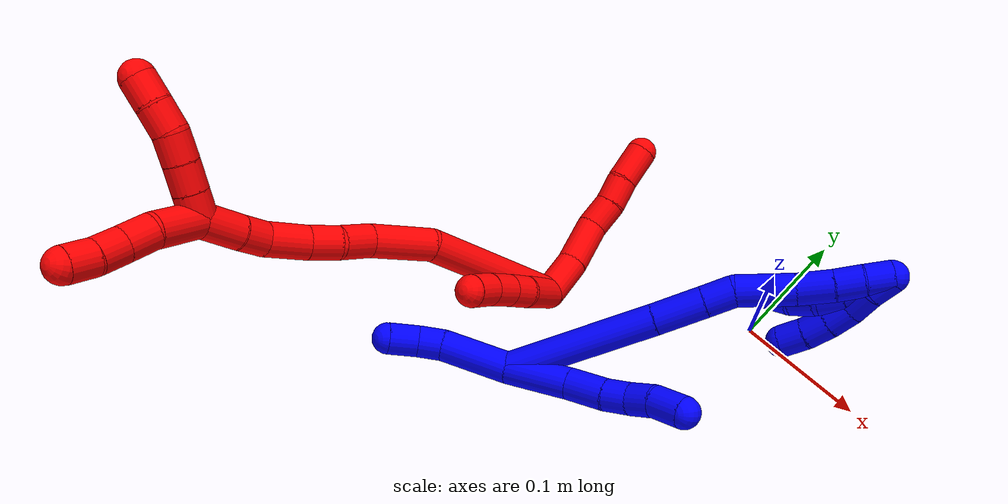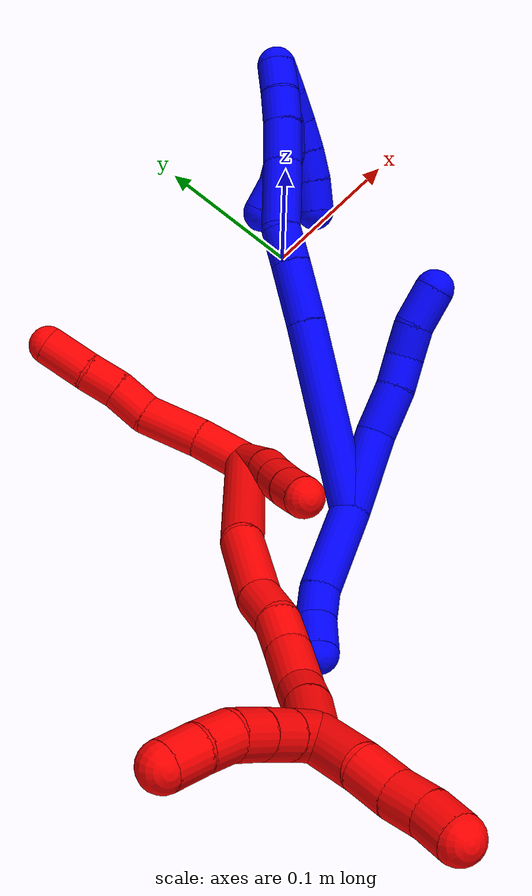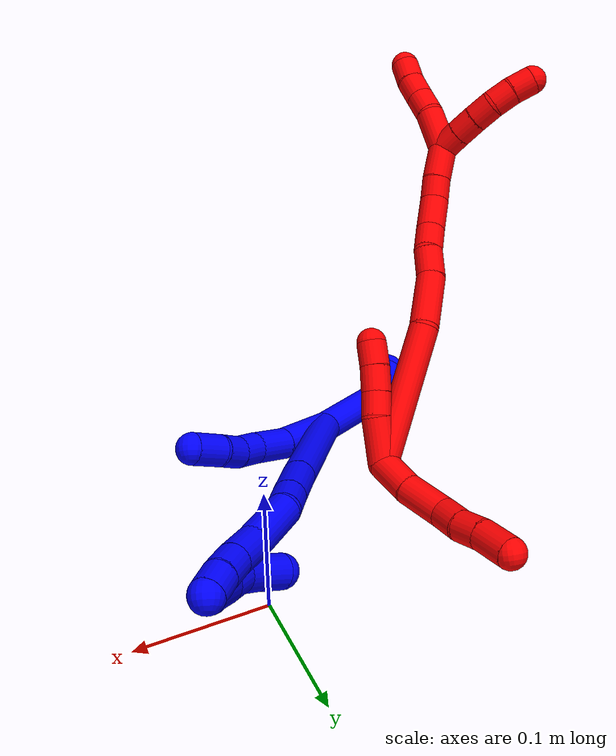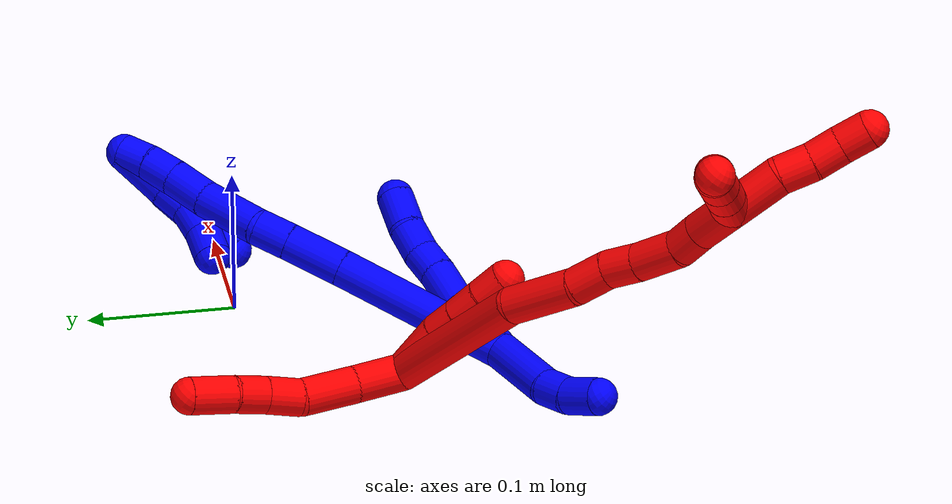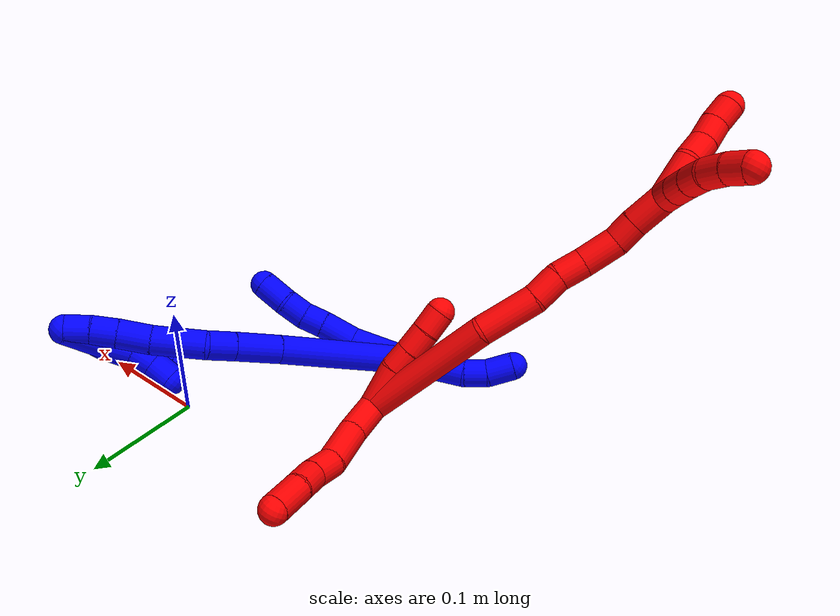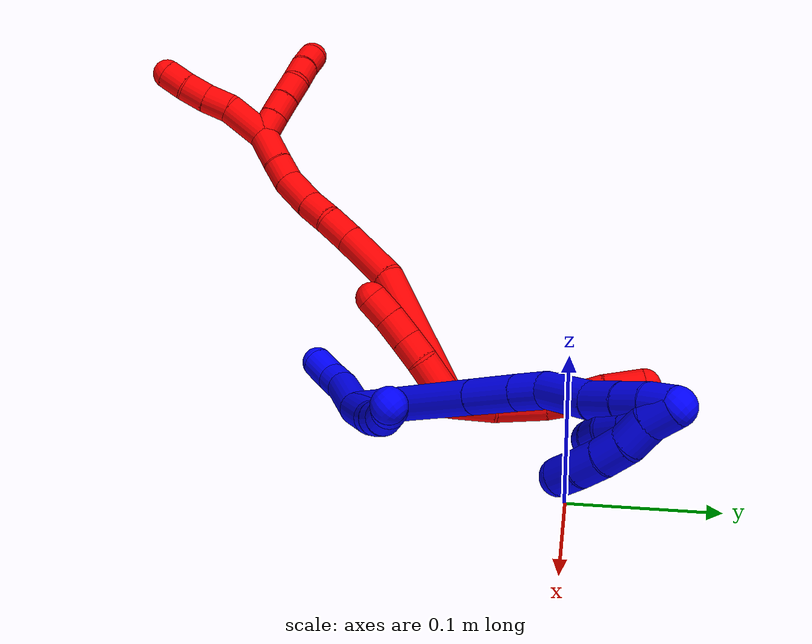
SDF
<sdf version="1.7">
 <world name="default">
  <plugin name="TubeGeneratorPlugin" filename="libtube_generator_plugin.so"/>
  <model name="photoneo_s_sensor">
   <static>1</static>
   <pose>0 0 2 1.57079 1.57079 3.14159</pose>
   <link name="link">
    <inertial><mass>0.1</mass></inertial>
    <sensor name="sensor" type="depth">
     <update_rate>30</update_rate>
     <camera>
      <horizontal_fov>1.22</horizontal_fov>
      <image><width>1920</width><height>1200</height><format>B8G8R8</format></image>
      <clip><near>0.1</near><far>4</far></clip>
      <depth_camera><output>points</output></depth_camera>
     </camera>
     <plugin name="camera_plugin" filename="libgazebo_ros_depth_camera.so">
      <baseline>0.2</baseline>
      <alwaysOn>1</alwaysOn>
      <updateRate>0.0</updateRate>
      <cameraName>camera_ir</cameraName>
      <imageTopicName>/camera/color/image_raw</imageTopicName>
      <cameraInfoTopicName>/camera/color/camera_info</cameraInfoTopicName>
      <depthImageTopicName>/camera/depth/image_raw</depthImageTopicName>
      <depthImageCameraInfoTopicName>/camera/depth/camera_info</depthImageCameraInfoTopicName>
      <pointCloudTopicName>/camera/depth/points</pointCloudTopicName>
      <frameName>fr_optical</frameName>
      <pointCloudCutoff>0.1</pointCloudCutoff>
      <pointCloudCutoffMax>2.0</pointCloudCutoffMax>
      <distortionK1>0</distortionK1>
      <distortionK2>0</distortionK2>
      <distortionK3>0</distortionK3>
      <distortionT1>0</distortionT1>
      <distortionT2>0</distortionT2>
      <CxPrime>0</CxPrime>
      <Cx>0</Cx>
      <Cy>0</Cy>
      <focalLength>0</focalLength>
      <hackBaseline>0</hackBaseline>
     </plugin>
    </sensor>
   </link>
  </model>
  <gravity>0 0 -9.8</gravity>
  <magnetic_field>6e-06 2.3e-05 -4.2e-05</magnetic_field>
  <atmosphere type="adiabatic"/>
  <physics name="default_physics" default="0" type="ode">
   <max_step_size>0.003</max_step_size>
   <real_time_factor>1</real_time_factor>
   <real_time_update_rate>1000</real_time_update_rate>
   <max_contacts>10000</max_contacts>
   <ode>
    <solver>
     <type>quick</type>
     <iters>100</iters>
     <sor>1.3</sor>
     <use_dynamic_moi_rescaling>0</use_dynamic_moi_rescaling>
    </solver>
    <constraints>
     <contact_max_correcting_vel>0</contact_max_correcting_vel>
     <contact_surface_layer>0.001</contact_surface_layer>
     <cfm>0</cfm>
     <erp>0.2</erp>
    </constraints>
   </ode>
  </physics>
  <scene><ambient>0.4 0.4 0.4 1</ambient><background>0.7 0.7 0.7 1</background><shadows>0</shadows></scene>
  <audio><device>default</device></audio>
  <spherical_coordinates>
   <surface_model>EARTH_WGS84</surface_model>
   <latitude_deg>0</latitude_deg>
   <longitude_deg>0</longitude_deg>
   <elevation>0</elevation>
   <heading_deg>0</heading_deg>
  </spherical_coordinates>
  <model name="bin">
   <static>1</static>
   <link name="bottom">
    <collision name="collision-bottom">
     <pose>0 0 -0.01 0 -0 0</pose>
     <geometry><box><size>0.8 0.6 0.02</size></box></geometry>
     <surface>
      <friction><ode><mu>100</mu><mu2>100</mu2></ode></friction>
      <contact><collide_bitmask>65535</collide_bitmask></contact>
     </surface>
    </collision>
   </link>
   <link name="west_wall">
    <collision name="collision-west_wall">
     <pose>-0.41 0 0.1 0 -0 0</pose>
     <geometry><box><size>0.02 0.6 0.2</size></box></geometry>
     <surface>
      <friction><ode><mu>100</mu><mu2>100</mu2></ode></friction>
      <contact><collide_bitmask>65535</collide_bitmask></contact>
     </surface>
    </collision>
   </link>
   <link name="east_wall">
    <collision name="collision-east_wall">
     <pose>0.41 0 0.1 0 -0 0</pose>
     <geometry><box><size>0.02 0.6 0.2</size></box></geometry>
     <surface>
      <friction><ode><mu>100</mu><mu2>100</mu2></ode></friction>
      <contact><collide_bitmask>65535</collide_bitmask></contact>
     </surface>
    </collision>
   </link>
   <link name="south_wall">
    <collision name="collision-south_wall">
     <pose>0 -0.31 0.1 0 -0 0</pose>
     <geometry><box><size>0.8 0.02 0.2</size></box></geometry>
     <surface>
      <friction><ode><mu>100</mu><mu2>100</mu2></ode></friction>
      <contact><collide_bitmask>65535</collide_bitmask></contact>
     </surface>
    </collision>
   </link>
   <link name="north_wall">
    <collision name="collision-north_wall">
     <pose>0 0.31 0.1 0 -0 0</pose>
     <geometry><box><size>0.8 0.02 0.2</size></box></geometry>
     <surface>
      <friction><ode><mu>100</mu><mu2>100</mu2></ode></friction>
      <contact><collide_bitmask>65535</collide_bitmask></contact>
     </surface>
    </collision>
   </link>
  </model>
  <model name="1">
   <static>0</static>
   <link name="1">
    <collision name="collision-cylinder-e_1_2_8">
     <pose>0.022806 0.005603 -0.010366 -2.64609 1.0939 -2.35416</pose>
     <geometry><cylinder><radius>0.0125</radius><length>0.05134</length></cylinder></geometry>
     <surface>
      <friction><ode><mu>1.16</mu><mu2>1.16</mu2><slip1>0</slip1><slip2>0</slip2></ode></friction>
      <contact><ode><kp>1e+06</kp><kd>1</kd><max_vel>0</max_vel><min_depth>0.001</min_depth></ode></contact>
     </surface>
    </collision>
    <visual name="visual-cylinder-e_1_2_8">
     <pose>0.022806 0.005603 -0.010366 -2.64609 1.0939 -2.35416</pose>
     <geometry><cylinder><radius>0.0125</radius><length>0.05134</length></cylinder></geometry>
     <material><ambient>0 0 1 1</ambient></material>
    </visual>
    <collision name="collision-cylinder-e_2_8_9">
     <pose>0.060382 0.014872 -0.024689 -2.39424 1.22063 -2.11965</pose>
     <geometry><cylinder><radius>0.0125</radius><length>0.031448</length></cylinder></geometry>
     <surface>
      <friction><ode><mu>1.16</mu><mu2>1.16</mu2><slip1>0</slip1><slip2>0</slip2></ode></friction>
      <contact><ode><kp>1e+06</kp><kd>1</kd><max_vel>0</max_vel><min_depth>0.001</min_depth></ode></contact>
     </surface>
    </collision>
    <visual name="visual-cylinder-e_2_8_9">
     <pose>0.060382 0.014872 -0.024689 -2.39424 1.22063 -2.11965</pose>
     <geometry><cylinder><radius>0.0125</radius><length>0.031448</length></cylinder></geometry>
     <material><ambient>0 0 1 1</ambient></material>
    </visual>
    <collision name="collision-cylinder-e_3_9_10">
     <pose>0.08419 0.021933 -0.031814 -2.32179 1.09614 -1.9044</pose>
     <geometry><cylinder><radius>0.0125</radius><length>0.020324</length></cylinder></geometry>
     <surface>
      <friction><ode><mu>1.16</mu><mu2>1.16</mu2><slip1>0</slip1><slip2>0</slip2></ode></friction>
      <contact><ode><kp>1e+06</kp><kd>1</kd><max_vel>0</max_vel><min_depth>0.001</min_depth></ode></contact>
     </surface>
    </collision>
    <visual name="visual-cylinder-e_3_9_10">
     <pose>0.08419 0.021933 -0.031814 -2.32179 1.09614 -1.9044</pose>
     <geometry><cylinder><radius>0.0125</radius><length>0.020324</length></cylinder></geometry>
     <material><ambient>0 0 1 1</ambient></material>
    </visual>
    <collision name="collision-cylinder-e_4_10_11">
     <pose>0.102473 0.029964 -0.036107 -1.80865 1.09442 -1.31817</pose>
     <geometry><cylinder><radius>0.0125</radius><length>0.020807</length></cylinder></geometry>
     <surface>
      <friction><ode><mu>1.16</mu><mu2>1.16</mu2><slip1>0</slip1><slip2>0</slip2></ode></friction>
      <contact><ode><kp>1e+06</kp><kd>1</kd><max_vel>0</max_vel><min_depth>0.001</min_depth></ode></contact>
     </surface>
    </collision>
    <visual name="visual-cylinder-e_4_10_11">
     <pose>0.102473 0.029964 -0.036107 -1.80865 1.09442 -1.31817</pose>
     <geometry><cylinder><radius>0.0125</radius><length>0.020807</length></cylinder></geometry>
     <material><ambient>0 0 1 1</ambient></material>
    </visual>
    <collision name="collision-cylinder-e_5_11_6">
     <pose>0.124389 0.037544 -0.03816 -1.87632 1.33187 -1.6399</pose>
     <geometry><cylinder><radius>0.0125</radius><length>0.026082</length></cylinder></geometry>
     <surface>
      <friction><ode><mu>1.16</mu><mu2>1.16</mu2><slip1>0</slip1><slip2>0</slip2></ode></friction>
      <contact><ode><kp>1e+06</kp><kd>1</kd><max_vel>0</max_vel><min_depth>0.001</min_depth></ode></contact>
     </surface>
    </collision>
    <visual name="visual-cylinder-e_5_11_6">
     <pose>0.124389 0.037544 -0.03816 -1.87632 1.33187 -1.6399</pose>
     <geometry><cylinder><radius>0.0125</radius><length>0.026082</length></cylinder></geometry>
     <material><ambient>0 0 1 1</ambient></material>
    </visual>
    <collision name="collision-cylinder-e_1_2_12">
     <pose>-0.023558 -0.002202 0.014157 0.154288 -1.02438 -0.086865</pose>
     <geometry><cylinder><radius>0.0125</radius><length>0.055145</length></cylinder></geometry>
     <surface>
      <friction><ode><mu>1.16</mu><mu2>1.16</mu2><slip1>0</slip1><slip2>0</slip2></ode></friction>
      <contact><ode><kp>1e+06</kp><kd>1</kd><max_vel>0</max_vel><min_depth>0.001</min_depth></ode></contact>
     </surface>
    </collision>
    <visual name="visual-cylinder-e_1_2_12">
     <pose>-0.023558 -0.002202 0.014157 0.154288 -1.02438 -0.086865</pose>
     <geometry><cylinder><radius>0.0125</radius><length>0.055145</length></cylinder></geometry>
     <material><ambient>0 0 1 1</ambient></material>
    </visual>
    <collision name="collision-cylinder-e_2_12_13">
     <pose>-0.054362 -0.006182 0.035402 0.245849 -0.781203 -0.101656</pose>
     <geometry><cylinder><radius>0.0125</radius><length>0.020582</length></cylinder></geometry>
     <surface>
      <friction><ode><mu>1.16</mu><mu2>1.16</mu2><slip1>0</slip1><slip2>0</slip2></ode></friction>
      <contact><ode><kp>1e+06</kp><kd>1</kd><max_vel>0</max_vel><min_depth>0.001</min_depth></ode></contact>
     </surface>
    </collision>
    <visual name="visual-cylinder-e_2_12_13">
     <pose>-0.054362 -0.006182 0.035402 0.245849 -0.781203 -0.101656</pose>
     <geometry><cylinder><radius>0.0125</radius><length>0.020582</length></cylinder></geometry>
     <material><ambient>0 0 1 1</ambient></material>
    </visual>
    <collision name="collision-cylinder-e_3_13_5">
     <pose>-0.06766 -0.009335 0.052919 0.131026 -0.522091 -0.035049</pose>
     <geometry><cylinder><radius>0.0125</radius><length>0.024273</length></cylinder></geometry>
     <surface>
      <friction><ode><mu>1.16</mu><mu2>1.16</mu2><slip1>0</slip1><slip2>0</slip2></ode></friction>
      <contact><ode><kp>1e+06</kp><kd>1</kd><max_vel>0</max_vel><min_depth>0.001</min_depth></ode></contact>
     </surface>
    </collision>
    <visual name="visual-cylinder-e_3_13_5">
     <pose>-0.06766 -0.009335 0.052919 0.131026 -0.522091 -0.035049</pose>
     <geometry><cylinder><radius>0.0125</radius><length>0.024273</length></cylinder></geometry>
     <material><ambient>0 0 1 1</ambient></material>
    </visual>
    <collision name="collision-cylinder-e_1_2_14">
     <pose>0.03353 0.038492 -0.031892 -2.26269 0.590843 -1.14902</pose>
     <geometry><cylinder><radius>0.0125</radius><length>0.120383</length></cylinder></geometry>
     <surface>
      <friction><ode><mu>1.16</mu><mu2>1.16</mu2><slip1>0</slip1><slip2>0</slip2></ode></friction>
      <contact><ode><kp>1e+06</kp><kd>1</kd><max_vel>0</max_vel><min_depth>0.001</min_depth></ode></contact>
     </surface>
    </collision>
    <visual name="visual-cylinder-e_1_2_14">
     <pose>0.03353 0.038492 -0.031892 -2.26269 0.590843 -1.14902</pose>
     <geometry><cylinder><radius>0.0125</radius><length>0.120383</length></cylinder></geometry>
     <material><ambient>0 0 1 1</ambient></material>
    </visual>
    <collision name="collision-cylinder-e_2_14_15">
     <pose>0.077789 0.089955 -0.074538 -2.26311 0.566968 -1.11005</pose>
     <geometry><cylinder><radius>0.0125</radius><length>0.03995</length></cylinder></geometry>
     <surface>
      <friction><ode><mu>1.16</mu><mu2>1.16</mu2><slip1>0</slip1><slip2>0</slip2></ode></friction>
      <contact><ode><kp>1e+06</kp><kd>1</kd><max_vel>0</max_vel><min_depth>0.001</min_depth></ode></contact>
     </surface>
    </collision>
    <visual name="visual-cylinder-e_2_14_15">
     <pose>0.077789 0.089955 -0.074538 -2.26311 0.566968 -1.11005</pose>
     <geometry><cylinder><radius>0.0125</radius><length>0.03995</length></cylinder></geometry>
     <material><ambient>0 0 1 1</ambient></material>
    </visual>
    <collision name="collision-cylinder-e_3_15_16">
     <pose>0.094788 0.110726 -0.091896 -2.27318 0.550427 -1.09394</pose>
     <geometry><cylinder><radius>0.0125</radius><length>0.023981</length></cylinder></geometry>
     <surface>
      <friction><ode><mu>1.16</mu><mu2>1.16</mu2><slip1>0</slip1><slip2>0</slip2></ode></friction>
      <contact><ode><kp>1e+06</kp><kd>1</kd><max_vel>0</max_vel><min_depth>0.001</min_depth></ode></contact>
     </surface>
    </collision>
    <visual name="visual-cylinder-e_3_15_16">
     <pose>0.094788 0.110726 -0.091896 -2.27318 0.550427 -1.09394</pose>
     <geometry><cylinder><radius>0.0125</radius><length>0.023981</length></cylinder></geometry>
     <material><ambient>0 0 1 1</ambient></material>
    </visual>
    <collision name="collision-cylinder-e_4_16_17">
     <pose>0.117168 0.127228 -0.112093 -2.57221 0.784367 -1.91007</pose>
     <geometry><cylinder><radius>0.0125</radius><length>0.045608</length></cylinder></geometry>
     <surface>
      <friction><ode><mu>1.16</mu><mu2>1.16</mu2><slip1>0</slip1><slip2>0</slip2></ode></friction>
      <contact><ode><kp>1e+06</kp><kd>1</kd><max_vel>0</max_vel><min_depth>0.001</min_depth></ode></contact>
     </surface>
    </collision>
    <visual name="visual-cylinder-e_4_16_17">
     <pose>0.117168 0.127228 -0.112093 -2.57221 0.784367 -1.91007</pose>
     <geometry><cylinder><radius>0.0125</radius><length>0.045608</length></cylinder></geometry>
     <material><ambient>0 0 1 1</ambient></material>
    </visual>
    <collision name="collision-cylinder-e_5_17_18">
     <pose>0.143382 0.142713 -0.132743 -2.37589 0.801444 -1.62142</pose>
     <geometry><cylinder><radius>0.0125</radius><length>0.028137</length></cylinder></geometry>
     <surface>
      <friction><ode><mu>1.16</mu><mu2>1.16</mu2><slip1>0</slip1><slip2>0</slip2></ode></friction>
      <contact><ode><kp>1e+06</kp><kd>1</kd><max_vel>0</max_vel><min_depth>0.001</min_depth></ode></contact>
     </surface>
    </collision>
    <visual name="visual-cylinder-e_5_17_18">
     <pose>0.143382 0.142713 -0.132743 -2.37589 0.801444 -1.62142</pose>
     <geometry><cylinder><radius>0.0125</radius><length>0.028137</length></cylinder></geometry>
     <material><ambient>0 0 1 1</ambient></material>
    </visual>
    <collision name="collision-cylinder-e_6_18_19">
     <pose>0.160625 0.155082 -0.145625 -2.37729 0.723941 -1.51123</pose>
     <geometry><cylinder><radius>0.0125</radius><length>0.021548</length></cylinder></geometry>
     <surface>
      <friction><ode><mu>1.16</mu><mu2>1.16</mu2><slip1>0</slip1><slip2>0</slip2></ode></friction>
      <contact><ode><kp>1e+06</kp><kd>1</kd><max_vel>0</max_vel><min_depth>0.001</min_depth></ode></contact>
     </surface>
    </collision>
    <visual name="visual-cylinder-e_6_18_19">
     <pose>0.160625 0.155082 -0.145625 -2.37729 0.723941 -1.51123</pose>
     <geometry><cylinder><radius>0.0125</radius><length>0.021548</length></cylinder></geometry>
     <material><ambient>0 0 1 1</ambient></material>
    </visual>
    <collision name="collision-cylinder-e_7_19_1">
     <pose>0.174011 0.165485 -0.15791 -2.5007 0.659867 -1.60214</pose>
     <geometry><cylinder><radius>0.0125</radius><length>0.020394</length></cylinder></geometry>
     <surface>
      <friction><ode><mu>1.16</mu><mu2>1.16</mu2><slip1>0</slip1><slip2>0</slip2></ode></friction>
      <contact><ode><kp>1e+06</kp><kd>1</kd><max_vel>0</max_vel><min_depth>0.001</min_depth></ode></contact>
     </surface>
    </collision>
    <visual name="visual-cylinder-e_7_19_1">
     <pose>0.174011 0.165485 -0.15791 -2.5007 0.659867 -1.60214</pose>
     <geometry><cylinder><radius>0.0125</radius><length>0.020394</length></cylinder></geometry>
     <material><ambient>0 0 1 1</ambient></material>
    </visual>
    <collision name="collision-cylinder-e_1_1_20">
     <pose>0.175881 0.161648 -0.161936 1.29692 -0.453562 -0.346212</pose>
     <geometry><cylinder><radius>0.0125</radius><length>0.02</length></cylinder></geometry>
     <surface>
      <friction><ode><mu>1.16</mu><mu2>1.16</mu2><slip1>0</slip1><slip2>0</slip2></ode></friction>
      <contact><ode><kp>1e+06</kp><kd>1</kd><max_vel>0</max_vel><min_depth>0.001</min_depth></ode></contact>
     </surface>
    </collision>
    <visual name="visual-cylinder-e_1_1_20">
     <pose>0.175881 0.161648 -0.161936 1.29692 -0.453562 -0.346212</pose>
     <geometry><cylinder><radius>0.0125</radius><length>0.02</length></cylinder></geometry>
     <material><ambient>0 0 1 1</ambient></material>
    </visual>
    <collision name="collision-cylinder-e_2_20_21">
     <pose>0.167436 0.143857 -0.159575 1.57845 -0.418413 -0.421536</pose>
     <geometry><cylinder><radius>0.0125</radius><length>0.02</length></cylinder></geometry>
     <surface>
      <friction><ode><mu>1.16</mu><mu2>1.16</mu2><slip1>0</slip1><slip2>0</slip2></ode></friction>
      <contact><ode><kp>1e+06</kp><kd>1</kd><max_vel>0</max_vel><min_depth>0.001</min_depth></ode></contact>
     </surface>
    </collision>
    <visual name="visual-cylinder-e_2_20_21">
     <pose>0.167436 0.143857 -0.159575 1.57845 -0.418413 -0.421536</pose>
     <geometry><cylinder><radius>0.0125</radius><length>0.02</length></cylinder></geometry>
     <material><ambient>0 0 1 1</ambient></material>
    </visual>
    <collision name="collision-cylinder-e_3_21_22">
     <pose>0.15859 0.126182 -0.157589 1.33446 -0.498718 -0.395962</pose>
     <geometry><cylinder><radius>0.0125</radius><length>0.02</length></cylinder></geometry>
     <surface>
      <friction><ode><mu>1.16</mu><mu2>1.16</mu2><slip1>0</slip1><slip2>0</slip2></ode></friction>
      <contact><ode><kp>1e+06</kp><kd>1</kd><max_vel>0</max_vel><min_depth>0.001</min_depth></ode></contact>
     </surface>
    </collision>
    <visual name="visual-cylinder-e_3_21_22">
     <pose>0.15859 0.126182 -0.157589 1.33446 -0.498718 -0.395962</pose>
     <geometry><cylinder><radius>0.0125</radius><length>0.02</length></cylinder></geometry>
     <material><ambient>0 0 1 1</ambient></material>
    </visual>
    <collision name="collision-cylinder-e_4_22_23">
     <pose>0.148272 0.109741 -0.152905 1.24987 -0.586493 -0.428946</pose>
     <geometry><cylinder><radius>0.0125</radius><length>0.02</length></cylinder></geometry>
     <surface>
      <friction><ode><mu>1.16</mu><mu2>1.16</mu2><slip1>0</slip1><slip2>0</slip2></ode></friction>
      <contact><ode><kp>1e+06</kp><kd>1</kd><max_vel>0</max_vel><min_depth>0.001</min_depth></ode></contact>
     </surface>
    </collision>
    <visual name="visual-cylinder-e_4_22_23">
     <pose>0.148272 0.109741 -0.152905 1.24987 -0.586493 -0.428946</pose>
     <geometry><cylinder><radius>0.0125</radius><length>0.02</length></cylinder></geometry>
     <material><ambient>0 0 1 1</ambient></material>
    </visual>
    <collision name="collision-cylinder-e_5_23_4">
     <pose>0.136186 0.094812 -0.147498 1.19404 -0.714414 -0.496921</pose>
     <geometry><cylinder><radius>0.0125</radius><length>0.02</length></cylinder></geometry>
     <surface>
      <friction><ode><mu>1.16</mu><mu2>1.16</mu2><slip1>0</slip1><slip2>0</slip2></ode></friction>
      <contact><ode><kp>1e+06</kp><kd>1</kd><max_vel>0</max_vel><min_depth>0.001</min_depth></ode></contact>
     </surface>
    </collision>
    <visual name="visual-cylinder-e_5_23_4">
     <pose>0.136186 0.094812 -0.147498 1.19404 -0.714414 -0.496921</pose>
     <geometry><cylinder><radius>0.0125</radius><length>0.02</length></cylinder></geometry>
     <material><ambient>0 0 1 1</ambient></material>
    </visual>
    <collision name="collision-cylinder-e_1_1_24">
     <pose>0.168591 0.156287 -0.159361 1.22769 -0.665057 -0.477428</pose>
     <geometry><cylinder><radius>0.0125</radius><length>0.037827</length></cylinder></geometry>
     <surface>
      <friction><ode><mu>1.16</mu><mu2>1.16</mu2><slip1>0</slip1><slip2>0</slip2></ode></friction>
      <contact><ode><kp>1e+06</kp><kd>1</kd><max_vel>0</max_vel><min_depth>0.001</min_depth></ode></contact>
     </surface>
    </collision>
    <visual name="visual-cylinder-e_1_1_24">
     <pose>0.168591 0.156287 -0.159361 1.22769 -0.665057 -0.477428</pose>
     <geometry><cylinder><radius>0.0125</radius><length>0.037827</length></cylinder></geometry>
     <material><ambient>0 0 1 1</ambient></material>
    </visual>
    <collision name="collision-cylinder-e_2_24_25">
     <pose>0.149337 0.13653 -0.150092 0.932238 -0.814736 -0.427541</pose>
     <geometry><cylinder><radius>0.0125</radius><length>0.020845</length></cylinder></geometry>
     <surface>
      <friction><ode><mu>1.16</mu><mu2>1.16</mu2><slip1>0</slip1><slip2>0</slip2></ode></friction>
      <contact><ode><kp>1e+06</kp><kd>1</kd><max_vel>0</max_vel><min_depth>0.001</min_depth></ode></contact>
     </surface>
    </collision>
    <visual name="visual-cylinder-e_2_24_25">
     <pose>0.149337 0.13653 -0.150092 0.932238 -0.814736 -0.427541</pose>
     <geometry><cylinder><radius>0.0125</radius><length>0.020845</length></cylinder></geometry>
     <material><ambient>0 0 1 1</ambient></material>
    </visual>
    <collision name="collision-cylinder-e_3_25_26">
     <pose>0.132901 0.126171 -0.144251 1.24129 -1.06698 -0.79903</pose>
     <geometry><cylinder><radius>0.0125</radius><length>0.020218</length></cylinder></geometry>
     <surface>
      <friction><ode><mu>1.16</mu><mu2>1.16</mu2><slip1>0</slip1><slip2>0</slip2></ode></friction>
      <contact><ode><kp>1e+06</kp><kd>1</kd><max_vel>0</max_vel><min_depth>0.001</min_depth></ode></contact>
     </surface>
    </collision>
    <visual name="visual-cylinder-e_3_25_26">
     <pose>0.132901 0.126171 -0.144251 1.24129 -1.06698 -0.79903</pose>
     <geometry><cylinder><radius>0.0125</radius><length>0.020218</length></cylinder></geometry>
     <material><ambient>0 0 1 1</ambient></material>
    </visual>
    <collision name="collision-cylinder-e_4_26_3">
     <pose>0.113821 0.119149 -0.14165 1.16873 -1.3207 -0.949107</pose>
     <geometry><cylinder><radius>0.0125</radius><length>0.02111</length></cylinder></geometry>
     <surface>
      <friction><ode><mu>1.16</mu><mu2>1.16</mu2><slip1>0</slip1><slip2>0</slip2></ode></friction>
      <contact><ode><kp>1e+06</kp><kd>1</kd><max_vel>0</max_vel><min_depth>0.001</min_depth></ode></contact>
     </surface>
    </collision>
    <visual name="visual-cylinder-e_4_26_3">
     <pose>0.113821 0.119149 -0.14165 1.16873 -1.3207 -0.949107</pose>
     <geometry><cylinder><radius>0.0125</radius><length>0.02111</length></cylinder></geometry>
     <material><ambient>0 0 1 1</ambient></material>
    </visual>
    <collision name="collision-sphere-3">
     <pose>0.103594 0.116745 -0.140627 0 -0 0</pose>
     <geometry><sphere><radius>0.0125</radius></sphere></geometry>
     <surface>
      <friction><ode><mu>1.16</mu><mu2>1.16</mu2><slip1>0</slip1><slip2>0</slip2></ode></friction>
      <contact><ode><kp>1e+06</kp><kd>1</kd><max_vel>0</max_vel><min_depth>0.001</min_depth></ode></contact>
     </surface>
    </collision>
    <visual name="visual-sphere-3">
     <pose>0.103594 0.116745 -0.140627 0 -0 0</pose>
     <geometry><sphere><radius>0.0125</radius></sphere></geometry>
     <material><ambient>0 0 1 1</ambient></material>
    </visual>
    <collision name="collision-sphere-26">
     <pose>0.124048 0.121553 -0.142672 0 -0 0</pose>
     <geometry><sphere><radius>0.0125</radius></sphere></geometry>
     <surface>
      <friction><ode><mu>1.16</mu><mu2>1.16</mu2><slip1>0</slip1><slip2>0</slip2></ode></friction>
      <contact><ode><kp>1e+06</kp><kd>1</kd><max_vel>0</max_vel><min_depth>0.001</min_depth></ode></contact>
     </surface>
    </collision>
    <visual name="visual-sphere-26">
     <pose>0.124048 0.121553 -0.142672 0 -0 0</pose>
     <geometry><sphere><radius>0.0125</radius></sphere></geometry>
     <material><ambient>0 0 1 1</ambient></material>
    </visual>
    <collision name="collision-sphere-25">
     <pose>0.141754 0.130789 -0.14583 0 -0 0</pose>
     <geometry><sphere><radius>0.0125</radius></sphere></geometry>
     <surface>
      <friction><ode><mu>1.16</mu><mu2>1.16</mu2><slip1>0</slip1><slip2>0</slip2></ode></friction>
      <contact><ode><kp>1e+06</kp><kd>1</kd><max_vel>0</max_vel><min_depth>0.001</min_depth></ode></contact>
     </surface>
    </collision>
    <visual name="visual-sphere-25">
     <pose>0.141754 0.130789 -0.14583 0 -0 0</pose>
     <geometry><sphere><radius>0.0125</radius></sphere></geometry>
     <material><ambient>0 0 1 1</ambient></material>
    </visual>
    <collision name="collision-sphere-24">
     <pose>0.15692 0.142272 -0.154354 0 -0 0</pose>
     <geometry><sphere><radius>0.0125</radius></sphere></geometry>
     <surface>
      <friction><ode><mu>1.16</mu><mu2>1.16</mu2><slip1>0</slip1><slip2>0</slip2></ode></friction>
      <contact><ode><kp>1e+06</kp><kd>1</kd><max_vel>0</max_vel><min_depth>0.001</min_depth></ode></contact>
     </surface>
    </collision>
    <visual name="visual-sphere-24">
     <pose>0.15692 0.142272 -0.154354 0 -0 0</pose>
     <geometry><sphere><radius>0.0125</radius></sphere></geometry>
     <material><ambient>0 0 1 1</ambient></material>
    </visual>
    <collision name="collision-sphere-4">
     <pose>0.129635 0.087787 -0.144719 0 -0 0</pose>
     <geometry><sphere><radius>0.0125</radius></sphere></geometry>
     <surface>
      <friction><ode><mu>1.16</mu><mu2>1.16</mu2><slip1>0</slip1><slip2>0</slip2></ode></friction>
      <contact><ode><kp>1e+06</kp><kd>1</kd><max_vel>0</max_vel><min_depth>0.001</min_depth></ode></contact>
     </surface>
    </collision>
    <visual name="visual-sphere-4">
     <pose>0.129635 0.087787 -0.144719 0 -0 0</pose>
     <geometry><sphere><radius>0.0125</radius></sphere></geometry>
     <material><ambient>0 0 1 1</ambient></material>
    </visual>
    <collision name="collision-sphere-23">
     <pose>0.142738 0.101837 -0.150278 0 -0 0</pose>
     <geometry><sphere><radius>0.0125</radius></sphere></geometry>
     <surface>
      <friction><ode><mu>1.16</mu><mu2>1.16</mu2><slip1>0</slip1><slip2>0</slip2></ode></friction>
      <contact><ode><kp>1e+06</kp><kd>1</kd><max_vel>0</max_vel><min_depth>0.001</min_depth></ode></contact>
     </surface>
    </collision>
    <visual name="visual-sphere-23">
     <pose>0.142738 0.101837 -0.150278 0 -0 0</pose>
     <geometry><sphere><radius>0.0125</radius></sphere></geometry>
     <material><ambient>0 0 1 1</ambient></material>
    </visual>
    <collision name="collision-sphere-22">
     <pose>0.153807 0.117644 -0.155533 0 -0 0</pose>
     <geometry><sphere><radius>0.0125</radius></sphere></geometry>
     <surface>
      <friction><ode><mu>1.16</mu><mu2>1.16</mu2><slip1>0</slip1><slip2>0</slip2></ode></friction>
      <contact><ode><kp>1e+06</kp><kd>1</kd><max_vel>0</max_vel><min_depth>0.001</min_depth></ode></contact>
     </surface>
    </collision>
    <visual name="visual-sphere-22">
     <pose>0.153807 0.117644 -0.155533 0 -0 0</pose>
     <geometry><sphere><radius>0.0125</radius></sphere></geometry>
     <material><ambient>0 0 1 1</ambient></material>
    </visual>
    <collision name="collision-sphere-21">
     <pose>0.163373 0.13472 -0.159645 0 -0 0</pose>
     <geometry><sphere><radius>0.0125</radius></sphere></geometry>
     <surface>
      <friction><ode><mu>1.16</mu><mu2>1.16</mu2><slip1>0</slip1><slip2>0</slip2></ode></friction>
      <contact><ode><kp>1e+06</kp><kd>1</kd><max_vel>0</max_vel><min_depth>0.001</min_depth></ode></contact>
     </surface>
    </collision>
    <visual name="visual-sphere-21">
     <pose>0.163373 0.13472 -0.159645 0 -0 0</pose>
     <geometry><sphere><radius>0.0125</radius></sphere></geometry>
     <material><ambient>0 0 1 1</ambient></material>
    </visual>
    <collision name="collision-sphere-20">
     <pose>0.171499 0.152994 -0.159505 0 -0 0</pose>
     <geometry><sphere><radius>0.0125</radius></sphere></geometry>
     <surface>
      <friction><ode><mu>1.16</mu><mu2>1.16</mu2><slip1>0</slip1><slip2>0</slip2></ode></friction>
      <contact><ode><kp>1e+06</kp><kd>1</kd><max_vel>0</max_vel><min_depth>0.001</min_depth></ode></contact>
     </surface>
    </collision>
    <visual name="visual-sphere-20">
     <pose>0.171499 0.152994 -0.159505 0 -0 0</pose>
     <geometry><sphere><radius>0.0125</radius></sphere></geometry>
     <material><ambient>0 0 1 1</ambient></material>
    </visual>
    <collision name="collision-sphere-6">
     <pose>0.137059 0.040487 -0.039088 0 -0 0</pose>
     <geometry><sphere><radius>0.0125</radius></sphere></geometry>
     <surface>
      <friction><ode><mu>1.16</mu><mu2>1.16</mu2><slip1>0</slip1><slip2>0</slip2></ode></friction>
      <contact><ode><kp>1e+06</kp><kd>1</kd><max_vel>0</max_vel><min_depth>0.001</min_depth></ode></contact>
     </surface>
    </collision>
    <visual name="visual-sphere-6">
     <pose>0.137059 0.040487 -0.039088 0 -0 0</pose>
     <geometry><sphere><radius>0.0125</radius></sphere></geometry>
     <material><ambient>0 0 1 1</ambient></material>
    </visual>
    <collision name="collision-sphere-11">
     <pose>0.111718 0.034601 -0.037231 0 -0 0</pose>
     <geometry><sphere><radius>0.0125</radius></sphere></geometry>
     <surface>
      <friction><ode><mu>1.16</mu><mu2>1.16</mu2><slip1>0</slip1><slip2>0</slip2></ode></friction>
      <contact><ode><kp>1e+06</kp><kd>1</kd><max_vel>0</max_vel><min_depth>0.001</min_depth></ode></contact>
     </surface>
    </collision>
    <visual name="visual-sphere-11">
     <pose>0.111718 0.034601 -0.037231 0 -0 0</pose>
     <geometry><sphere><radius>0.0125</radius></sphere></geometry>
     <material><ambient>0 0 1 1</ambient></material>
    </visual>
    <collision name="collision-sphere-10">
     <pose>0.093228 0.025328 -0.034983 0 -0 0</pose>
     <geometry><sphere><radius>0.0125</radius></sphere></geometry>
     <surface>
      <friction><ode><mu>1.16</mu><mu2>1.16</mu2><slip1>0</slip1><slip2>0</slip2></ode></friction>
      <contact><ode><kp>1e+06</kp><kd>1</kd><max_vel>0</max_vel><min_depth>0.001</min_depth></ode></contact>
     </surface>
    </collision>
    <visual name="visual-sphere-10">
     <pose>0.093228 0.025328 -0.034983 0 -0 0</pose>
     <geometry><sphere><radius>0.0125</radius></sphere></geometry>
     <material><ambient>0 0 1 1</ambient></material>
    </visual>
    <collision name="collision-sphere-9">
     <pose>0.075151 0.018538 -0.028645 0 -0 0</pose>
     <geometry><sphere><radius>0.0125</radius></sphere></geometry>
     <surface>
      <friction><ode><mu>1.16</mu><mu2>1.16</mu2><slip1>0</slip1><slip2>0</slip2></ode></friction>
      <contact><ode><kp>1e+06</kp><kd>1</kd><max_vel>0</max_vel><min_depth>0.001</min_depth></ode></contact>
     </surface>
    </collision>
    <visual name="visual-sphere-9">
     <pose>0.075151 0.018538 -0.028645 0 -0 0</pose>
     <geometry><sphere><radius>0.0125</radius></sphere></geometry>
     <material><ambient>0 0 1 1</ambient></material>
    </visual>
    <collision name="collision-sphere-2">
     <geometry><sphere><radius>0.0125</radius></sphere></geometry>
     <surface>
      <friction><ode><mu>1.16</mu><mu2>1.16</mu2><slip1>0</slip1><slip2>0</slip2></ode></friction>
      <contact><ode><kp>1e+06</kp><kd>1</kd><max_vel>0</max_vel><min_depth>0.001</min_depth></ode></contact>
     </surface>
    </collision>
    <visual name="visual-sphere-2">
     <geometry><sphere><radius>0.0125</radius></sphere></geometry>
     <material><ambient>0 0 1 1</ambient></material>
    </visual>
    <collision name="collision-sphere-19">
     <pose>0.16776 0.160668 -0.151452 0 -0 0</pose>
     <geometry><sphere><radius>0.0125</radius></sphere></geometry>
     <surface>
      <friction><ode><mu>1.16</mu><mu2>1.16</mu2><slip1>0</slip1><slip2>0</slip2></ode></friction>
      <contact><ode><kp>1e+06</kp><kd>1</kd><max_vel>0</max_vel><min_depth>0.001</min_depth></ode></contact>
     </surface>
    </collision>
    <visual name="visual-sphere-19">
     <pose>0.16776 0.160668 -0.151452 0 -0 0</pose>
     <geometry><sphere><radius>0.0125</radius></sphere></geometry>
     <material><ambient>0 0 1 1</ambient></material>
    </visual>
    <collision name="collision-sphere-8">
     <pose>0.045612 0.011205 -0.020732 0 -0 0</pose>
     <geometry><sphere><radius>0.0125</radius></sphere></geometry>
     <surface>
      <friction><ode><mu>1.16</mu><mu2>1.16</mu2><slip1>0</slip1><slip2>0</slip2></ode></friction>
      <contact><ode><kp>1e+06</kp><kd>1</kd><max_vel>0</max_vel><min_depth>0.001</min_depth></ode></contact>
     </surface>
    </collision>
    <visual name="visual-sphere-8">
     <pose>0.045612 0.011205 -0.020732 0 -0 0</pose>
     <geometry><sphere><radius>0.0125</radius></sphere></geometry>
     <material><ambient>0 0 1 1</ambient></material>
    </visual>
    <collision name="collision-sphere-12">
     <pose>-0.047115 -0.004404 0.028314 0 -0 0</pose>
     <geometry><sphere><radius>0.0125</radius></sphere></geometry>
     <surface>
      <friction><ode><mu>1.16</mu><mu2>1.16</mu2><slip1>0</slip1><slip2>0</slip2></ode></friction>
      <contact><ode><kp>1e+06</kp><kd>1</kd><max_vel>0</max_vel><min_depth>0.001</min_depth></ode></contact>
     </surface>
    </collision>
    <visual name="visual-sphere-12">
     <pose>-0.047115 -0.004404 0.028314 0 -0 0</pose>
     <geometry><sphere><radius>0.0125</radius></sphere></geometry>
     <material><ambient>0 0 1 1</ambient></material>
    </visual>
    <collision name="collision-sphere-13">
     <pose>-0.061608 -0.00796 0.042489 0 -0 0</pose>
     <geometry><sphere><radius>0.0125</radius></sphere></geometry>
     <surface>
      <friction><ode><mu>1.16</mu><mu2>1.16</mu2><slip1>0</slip1><slip2>0</slip2></ode></friction>
      <contact><ode><kp>1e+06</kp><kd>1</kd><max_vel>0</max_vel><min_depth>0.001</min_depth></ode></contact>
     </surface>
    </collision>
    <visual name="visual-sphere-13">
     <pose>-0.061608 -0.00796 0.042489 0 -0 0</pose>
     <geometry><sphere><radius>0.0125</radius></sphere></geometry>
     <material><ambient>0 0 1 1</ambient></material>
    </visual>
    <collision name="collision-sphere-5">
     <pose>-0.073713 -0.010709 0.063349 0 -0 0</pose>
     <geometry><sphere><radius>0.0125</radius></sphere></geometry>
     <surface>
      <friction><ode><mu>1.16</mu><mu2>1.16</mu2><slip1>0</slip1><slip2>0</slip2></ode></friction>
      <contact><ode><kp>1e+06</kp><kd>1</kd><max_vel>0</max_vel><min_depth>0.001</min_depth></ode></contact>
     </surface>
    </collision>
    <visual name="visual-sphere-5">
     <pose>-0.073713 -0.010709 0.063349 0 -0 0</pose>
     <geometry><sphere><radius>0.0125</radius></sphere></geometry>
     <material><ambient>0 0 1 1</ambient></material>
    </visual>
    <collision name="collision-sphere-14">
     <pose>0.067061 0.076985 -0.063783 0 -0 0</pose>
     <geometry><sphere><radius>0.0125</radius></sphere></geometry>
     <surface>
      <friction><ode><mu>1.16</mu><mu2>1.16</mu2><slip1>0</slip1><slip2>0</slip2></ode></friction>
      <contact><ode><kp>1e+06</kp><kd>1</kd><max_vel>0</max_vel><min_depth>0.001</min_depth></ode></contact>
     </surface>
    </collision>
    <visual name="visual-sphere-14">
     <pose>0.067061 0.076985 -0.063783 0 -0 0</pose>
     <geometry><sphere><radius>0.0125</radius></sphere></geometry>
     <material><ambient>0 0 1 1</ambient></material>
    </visual>
    <collision name="collision-sphere-15">
     <pose>0.088517 0.102925 -0.085294 0 -0 0</pose>
     <geometry><sphere><radius>0.0125</radius></sphere></geometry>
     <surface>
      <friction><ode><mu>1.16</mu><mu2>1.16</mu2><slip1>0</slip1><slip2>0</slip2></ode></friction>
      <contact><ode><kp>1e+06</kp><kd>1</kd><max_vel>0</max_vel><min_depth>0.001</min_depth></ode></contact>
     </surface>
    </collision>
    <visual name="visual-sphere-15">
     <pose>0.088517 0.102925 -0.085294 0 -0 0</pose>
     <geometry><sphere><radius>0.0125</radius></sphere></geometry>
     <material><ambient>0 0 1 1</ambient></material>
    </visual>
    <collision name="collision-sphere-16">
     <pose>0.10106 0.118526 -0.098498 0 -0 0</pose>
     <geometry><sphere><radius>0.0125</radius></sphere></geometry>
     <surface>
      <friction><ode><mu>1.16</mu><mu2>1.16</mu2><slip1>0</slip1><slip2>0</slip2></ode></friction>
      <contact><ode><kp>1e+06</kp><kd>1</kd><max_vel>0</max_vel><min_depth>0.001</min_depth></ode></contact>
     </surface>
    </collision>
    <visual name="visual-sphere-16">
     <pose>0.10106 0.118526 -0.098498 0 -0 0</pose>
     <geometry><sphere><radius>0.0125</radius></sphere></geometry>
     <material><ambient>0 0 1 1</ambient></material>
    </visual>
    <collision name="collision-sphere-17">
     <pose>0.133276 0.13593 -0.125688 0 -0 0</pose>
     <geometry><sphere><radius>0.0125</radius></sphere></geometry>
     <surface>
      <friction><ode><mu>1.16</mu><mu2>1.16</mu2><slip1>0</slip1><slip2>0</slip2></ode></friction>
      <contact><ode><kp>1e+06</kp><kd>1</kd><max_vel>0</max_vel><min_depth>0.001</min_depth></ode></contact>
     </surface>
    </collision>
    <visual name="visual-sphere-17">
     <pose>0.133276 0.13593 -0.125688 0 -0 0</pose>
     <geometry><sphere><radius>0.0125</radius></sphere></geometry>
     <material><ambient>0 0 1 1</ambient></material>
    </visual>
    <collision name="collision-sphere-18">
     <pose>0.153489 0.149496 -0.139798 0 -0 0</pose>
     <geometry><sphere><radius>0.0125</radius></sphere></geometry>
     <surface>
      <friction><ode><mu>1.16</mu><mu2>1.16</mu2><slip1>0</slip1><slip2>0</slip2></ode></friction>
      <contact><ode><kp>1e+06</kp><kd>1</kd><max_vel>0</max_vel><min_depth>0.001</min_depth></ode></contact>
     </surface>
    </collision>
    <visual name="visual-sphere-18">
     <pose>0.153489 0.149496 -0.139798 0 -0 0</pose>
     <geometry><sphere><radius>0.0125</radius></sphere></geometry>
     <material><ambient>0 0 1 1</ambient></material>
    </visual>
    <collision name="collision-sphere-1">
     <pose>0.180263 0.170302 -0.164368 0 -0 0</pose>
     <geometry><sphere><radius>0.0125</radius></sphere></geometry>
     <surface>
      <friction><ode><mu>1.16</mu><mu2>1.16</mu2><slip1>0</slip1><slip2>0</slip2></ode></friction>
      <contact><ode><kp>1e+06</kp><kd>1</kd><max_vel>0</max_vel><min_depth>0.001</min_depth></ode></contact>
     </surface>
    </collision>
    <visual name="visual-sphere-1">
     <pose>0.180263 0.170302 -0.164368 0 -0 0</pose>
     <geometry><sphere><radius>0.0125</radius></sphere></geometry>
     <material><ambient>0 0 1 1</ambient></material>
    </visual>
    <inertial>
     <pose>0.082946 0.07506 -0.074384 0 -0 0</pose>
     <mass>0.75</mass>
     <inertia>
      <ixx>-6.7e-05</ixx>
      <ixy>0</ixy>
      <ixz>0</ixz>
      <iyy>-6.1e-05</iyy>
      <iyz>0</iyz>
      <izz>-0.0002</izz>
     </inertia>
    </inertial>
   </link>
   <pose>-0.116155 -0.160459 0.014177 0.834797 -0.359327 -0.067689</pose>
  </model>
  <model name="2">
   <static>0</static>
   <link name="2">
    <collision name="collision-cylinder-e_1_2_8">
     <pose>-0.004199 0.012578 -0.010666 -2.27415 -0.249298 0.528443</pose>
     <geometry><cylinder><radius>0.0125</radius><length>0.034035</length></cylinder></geometry>
     <surface>
      <friction><ode><mu>1.16</mu><mu2>1.16</mu2><slip1>0</slip1><slip2>0</slip2></ode></friction>
      <contact><ode><kp>1e+06</kp><kd>1</kd><max_vel>0</max_vel><min_depth>0.001</min_depth></ode></contact>
     </surface>
    </collision>
    <visual name="visual-cylinder-e_1_2_8">
     <pose>-0.004199 0.012578 -0.010666 -2.27415 -0.249298 0.528443</pose>
     <geometry><cylinder><radius>0.0125</radius><length>0.034035</length></cylinder></geometry>
     <material><ambient>1 0 0 1</ambient></material>
    </visual>
    <collision name="collision-cylinder-e_2_8_9">
     <pose>-0.015344 0.040091 -0.031378 -2.16289 -0.368304 0.672904</pose>
     <geometry><cylinder><radius>0.0125</radius><length>0.038587</length></cylinder></geometry>
     <surface>
      <friction><ode><mu>1.16</mu><mu2>1.16</mu2><slip1>0</slip1><slip2>0</slip2></ode></friction>
      <contact><ode><kp>1e+06</kp><kd>1</kd><max_vel>0</max_vel><min_depth>0.001</min_depth></ode></contact>
     </surface>
    </collision>
    <visual name="visual-cylinder-e_2_8_9">
     <pose>-0.015344 0.040091 -0.031378 -2.16289 -0.368304 0.672904</pose>
     <geometry><cylinder><radius>0.0125</radius><length>0.038587</length></cylinder></geometry>
     <material><ambient>1 0 0 1</ambient></material>
    </visual>
    <collision name="collision-cylinder-e_3_9_10">
     <pose>-0.02376 0.066192 -0.046122 -1.96913 -0.120772 0.181577</pose>
     <geometry><cylinder><radius>0.0125</radius><length>0.024405</length></cylinder></geometry>
     <surface>
      <friction><ode><mu>1.16</mu><mu2>1.16</mu2><slip1>0</slip1><slip2>0</slip2></ode></friction>
      <contact><ode><kp>1e+06</kp><kd>1</kd><max_vel>0</max_vel><min_depth>0.001</min_depth></ode></contact>
     </surface>
    </collision>
    <visual name="visual-cylinder-e_3_9_10">
     <pose>-0.02376 0.066192 -0.046122 -1.96913 -0.120772 0.181577</pose>
     <geometry><cylinder><radius>0.0125</radius><length>0.024405</length></cylinder></geometry>
     <material><ambient>1 0 0 1</ambient></material>
    </visual>
    <collision name="collision-cylinder-e_4_10_11">
     <pose>-0.028659 0.087509 -0.054242 -1.89585 -0.309797 0.428142</pose>
     <geometry><cylinder><radius>0.0125</radius><length>0.022497</length></cylinder></geometry>
     <surface>
      <friction><ode><mu>1.16</mu><mu2>1.16</mu2><slip1>0</slip1><slip2>0</slip2></ode></friction>
      <contact><ode><kp>1e+06</kp><kd>1</kd><max_vel>0</max_vel><min_depth>0.001</min_depth></ode></contact>
     </surface>
    </collision>
    <visual name="visual-cylinder-e_4_10_11">
     <pose>-0.028659 0.087509 -0.054242 -1.89585 -0.309797 0.428142</pose>
     <geometry><cylinder><radius>0.0125</radius><length>0.022497</length></cylinder></geometry>
     <material><ambient>1 0 0 1</ambient></material>
    </visual>
    <collision name="collision-cylinder-e_5_11_6">
     <pose>-0.035583 0.111019 -0.064111 -2.02048 -0.231353 0.366066</pose>
     <geometry><cylinder><radius>0.0125</radius><length>0.030476</length></cylinder></geometry>
     <surface>
      <friction><ode><mu>1.16</mu><mu2>1.16</mu2><slip1>0</slip1><slip2>0</slip2></ode></friction>
      <contact><ode><kp>1e+06</kp><kd>1</kd><max_vel>0</max_vel><min_depth>0.001</min_depth></ode></contact>
     </surface>
    </collision>
    <visual name="visual-cylinder-e_5_11_6">
     <pose>-0.035583 0.111019 -0.064111 -2.02048 -0.231353 0.366066</pose>
     <geometry><cylinder><radius>0.0125</radius><length>0.030476</length></cylinder></geometry>
     <material><ambient>1 0 0 1</ambient></material>
    </visual>
    <collision name="collision-cylinder-e_1_2_12">
     <pose>-0.000221 -0.000451 0.018875 0.023872 -0.011704 -0.00014</pose>
     <geometry><cylinder><radius>0.0125</radius><length>0.037763</length></cylinder></geometry>
     <surface>
      <friction><ode><mu>1.16</mu><mu2>1.16</mu2><slip1>0</slip1><slip2>0</slip2></ode></friction>
      <contact><ode><kp>1e+06</kp><kd>1</kd><max_vel>0</max_vel><min_depth>0.001</min_depth></ode></contact>
     </surface>
    </collision>
    <visual name="visual-cylinder-e_1_2_12">
     <pose>-0.000221 -0.000451 0.018875 0.023872 -0.011704 -0.00014</pose>
     <geometry><cylinder><radius>0.0125</radius><length>0.037763</length></cylinder></geometry>
     <material><ambient>1 0 0 1</ambient></material>
    </visual>
    <collision name="collision-cylinder-e_2_12_13">
     <pose>-0.00232 -0.00215 0.04751 0.127265 -0.188589 -0.012052</pose>
     <geometry><cylinder><radius>0.0125</radius><length>0.020036</length></cylinder></geometry>
     <surface>
      <friction><ode><mu>1.16</mu><mu2>1.16</mu2><slip1>0</slip1><slip2>0</slip2></ode></friction>
      <contact><ode><kp>1e+06</kp><kd>1</kd><max_vel>0</max_vel><min_depth>0.001</min_depth></ode></contact>
     </surface>
    </collision>
    <visual name="visual-cylinder-e_2_12_13">
     <pose>-0.00232 -0.00215 0.04751 0.127265 -0.188589 -0.012052</pose>
     <geometry><cylinder><radius>0.0125</radius><length>0.020036</length></cylinder></geometry>
     <material><ambient>1 0 0 1</ambient></material>
    </visual>
    <collision name="collision-cylinder-e_3_13_14">
     <pose>-0.005698 -0.004767 0.06794 0.127465 -0.138548 -0.008856</pose>
     <geometry><cylinder><radius>0.0125</radius><length>0.021721</length></cylinder></geometry>
     <surface>
      <friction><ode><mu>1.16</mu><mu2>1.16</mu2><slip1>0</slip1><slip2>0</slip2></ode></friction>
      <contact><ode><kp>1e+06</kp><kd>1</kd><max_vel>0</max_vel><min_depth>0.001</min_depth></ode></contact>
     </surface>
    </collision>
    <visual name="visual-cylinder-e_3_13_14">
     <pose>-0.005698 -0.004767 0.06794 0.127465 -0.138548 -0.008856</pose>
     <geometry><cylinder><radius>0.0125</radius><length>0.021721</length></cylinder></geometry>
     <material><ambient>1 0 0 1</ambient></material>
    </visual>
    <collision name="collision-cylinder-e_4_14_5">
     <pose>-0.007891 -0.00791 0.088671 0.174729 -0.067682 -0.00593</pose>
     <geometry><cylinder><radius>0.0125</radius><length>0.02048</length></cylinder></geometry>
     <surface>
      <friction><ode><mu>1.16</mu><mu2>1.16</mu2><slip1>0</slip1><slip2>0</slip2></ode></friction>
      <contact><ode><kp>1e+06</kp><kd>1</kd><max_vel>0</max_vel><min_depth>0.001</min_depth></ode></contact>
     </surface>
    </collision>
    <visual name="visual-cylinder-e_4_14_5">
     <pose>-0.007891 -0.00791 0.088671 0.174729 -0.067682 -0.00593</pose>
     <geometry><cylinder><radius>0.0125</radius><length>0.02048</length></cylinder></geometry>
     <material><ambient>1 0 0 1</ambient></material>
    </visual>
    <collision name="collision-cylinder-e_1_2_15">
     <pose>-0.027298 -0.001665 0.052958 0.03143 -0.47574 -0.007621</pose>
     <geometry><cylinder><radius>0.0125</radius><length>0.119205</length></cylinder></geometry>
     <surface>
      <friction><ode><mu>1.16</mu><mu2>1.16</mu2><slip1>0</slip1><slip2>0</slip2></ode></friction>
      <contact><ode><kp>1e+06</kp><kd>1</kd><max_vel>0</max_vel><min_depth>0.001</min_depth></ode></contact>
     </surface>
    </collision>
    <visual name="visual-cylinder-e_1_2_15">
     <pose>-0.027298 -0.001665 0.052958 0.03143 -0.47574 -0.007621</pose>
     <geometry><cylinder><radius>0.0125</radius><length>0.119205</length></cylinder></geometry>
     <material><ambient>1 0 0 1</ambient></material>
    </visual>
    <collision name="collision-cylinder-e_2_15_16">
     <pose>-0.064739 -0.011321 0.127371 0.35652 -0.417059 -0.076214</pose>
     <geometry><cylinder><radius>0.0125</radius><length>0.050083</length></cylinder></geometry>
     <surface>
      <friction><ode><mu>1.16</mu><mu2>1.16</mu2><slip1>0</slip1><slip2>0</slip2></ode></friction>
      <contact><ode><kp>1e+06</kp><kd>1</kd><max_vel>0</max_vel><min_depth>0.001</min_depth></ode></contact>
     </surface>
    </collision>
    <visual name="visual-cylinder-e_2_15_16">
     <pose>-0.064739 -0.011321 0.127371 0.35652 -0.417059 -0.076214</pose>
     <geometry><cylinder><radius>0.0125</radius><length>0.050083</length></cylinder></geometry>
     <material><ambient>1 0 0 1</ambient></material>
    </visual>
    <collision name="collision-cylinder-e_3_16_17">
     <pose>-0.077181 -0.023206 0.160795 0.314603 -0.180558 -0.028715</pose>
     <geometry><cylinder><radius>0.0125</radius><length>0.025588</length></cylinder></geometry>
     <surface>
      <friction><ode><mu>1.16</mu><mu2>1.16</mu2><slip1>0</slip1><slip2>0</slip2></ode></friction>
      <contact><ode><kp>1e+06</kp><kd>1</kd><max_vel>0</max_vel><min_depth>0.001</min_depth></ode></contact>
     </surface>
    </collision>
    <visual name="visual-cylinder-e_3_16_17">
     <pose>-0.077181 -0.023206 0.160795 0.314603 -0.180558 -0.028715</pose>
     <geometry><cylinder><radius>0.0125</radius><length>0.025588</length></cylinder></geometry>
     <material><ambient>1 0 0 1</ambient></material>
    </visual>
    <collision name="collision-cylinder-e_4_17_18">
     <pose>-0.084052 -0.031573 0.182468 0.431824 -0.404438 -0.089874</pose>
     <geometry><cylinder><radius>0.0125</radius><length>0.023246</length></cylinder></geometry>
     <surface>
      <friction><ode><mu>1.16</mu><mu2>1.16</mu2><slip1>0</slip1><slip2>0</slip2></ode></friction>
      <contact><ode><kp>1e+06</kp><kd>1</kd><max_vel>0</max_vel><min_depth>0.001</min_depth></ode></contact>
     </surface>
    </collision>
    <visual name="visual-cylinder-e_4_17_18">
     <pose>-0.084052 -0.031573 0.182468 0.431824 -0.404438 -0.089874</pose>
     <geometry><cylinder><radius>0.0125</radius><length>0.023246</length></cylinder></geometry>
     <material><ambient>1 0 0 1</ambient></material>
    </visual>
    <collision name="collision-cylinder-e_5_18_19">
     <pose>-0.094752 -0.040557 0.205929 0.316918 -0.400304 -0.064813</pose>
     <geometry><cylinder><radius>0.0125</radius><length>0.031442</length></cylinder></geometry>
     <surface>
      <friction><ode><mu>1.16</mu><mu2>1.16</mu2><slip1>0</slip1><slip2>0</slip2></ode></friction>
      <contact><ode><kp>1e+06</kp><kd>1</kd><max_vel>0</max_vel><min_depth>0.001</min_depth></ode></contact>
     </surface>
    </collision>
    <visual name="visual-cylinder-e_5_18_19">
     <pose>-0.094752 -0.040557 0.205929 0.316918 -0.400304 -0.064813</pose>
     <geometry><cylinder><radius>0.0125</radius><length>0.031442</length></cylinder></geometry>
     <material><ambient>1 0 0 1</ambient></material>
    </visual>
    <collision name="collision-cylinder-e_6_19_20">
     <pose>-0.103657 -0.045343 0.22941 0.028181 -0.278273 -0.003947</pose>
     <geometry><cylinder><radius>0.0125</radius><length>0.020235</length></cylinder></geometry>
     <surface>
      <friction><ode><mu>1.16</mu><mu2>1.16</mu2><slip1>0</slip1><slip2>0</slip2></ode></friction>
      <contact><ode><kp>1e+06</kp><kd>1</kd><max_vel>0</max_vel><min_depth>0.001</min_depth></ode></contact>
     </surface>
    </collision>
    <visual name="visual-cylinder-e_6_19_20">
     <pose>-0.103657 -0.045343 0.22941 0.028181 -0.278273 -0.003947</pose>
     <geometry><cylinder><radius>0.0125</radius><length>0.020235</length></cylinder></geometry>
     <material><ambient>1 0 0 1</ambient></material>
    </visual>
    <collision name="collision-cylinder-e_7_20_1">
     <pose>-0.112041 -0.046103 0.253148 0.034665 -0.380267 -0.006672</pose>
     <geometry><cylinder><radius>0.0125</radius><length>0.030201</length></cylinder></geometry>
     <surface>
      <friction><ode><mu>1.16</mu><mu2>1.16</mu2><slip1>0</slip1><slip2>0</slip2></ode></friction>
      <contact><ode><kp>1e+06</kp><kd>1</kd><max_vel>0</max_vel><min_depth>0.001</min_depth></ode></contact>
     </surface>
    </collision>
    <visual name="visual-cylinder-e_7_20_1">
     <pose>-0.112041 -0.046103 0.253148 0.034665 -0.380267 -0.006672</pose>
     <geometry><cylinder><radius>0.0125</radius><length>0.030201</length></cylinder></geometry>
     <material><ambient>1 0 0 1</ambient></material>
    </visual>
    <collision name="collision-cylinder-e_1_1_21">
     <pose>-0.123182 -0.039704 0.271847 -0.973232 -0.586615 0.316886</pose>
     <geometry><cylinder><radius>0.0125</radius><length>0.02</length></cylinder></geometry>
     <surface>
      <friction><ode><mu>1.16</mu><mu2>1.16</mu2><slip1>0</slip1><slip2>0</slip2></ode></friction>
      <contact><ode><kp>1e+06</kp><kd>1</kd><max_vel>0</max_vel><min_depth>0.001</min_depth></ode></contact>
     </surface>
    </collision>
    <visual name="visual-cylinder-e_1_1_21">
     <pose>-0.123182 -0.039704 0.271847 -0.973232 -0.586615 0.316886</pose>
     <geometry><cylinder><radius>0.0125</radius><length>0.02</length></cylinder></geometry>
     <material><ambient>1 0 0 1</ambient></material>
    </visual>
    <collision name="collision-cylinder-e_2_21_22">
     <pose>-0.134466 -0.025992 0.281044 -0.986891 -0.612498 0.336892</pose>
     <geometry><cylinder><radius>0.0125</radius><length>0.02</length></cylinder></geometry>
     <surface>
      <friction><ode><mu>1.16</mu><mu2>1.16</mu2><slip1>0</slip1><slip2>0</slip2></ode></friction>
      <contact><ode><kp>1e+06</kp><kd>1</kd><max_vel>0</max_vel><min_depth>0.001</min_depth></ode></contact>
     </surface>
    </collision>
    <visual name="visual-cylinder-e_2_21_22">
     <pose>-0.134466 -0.025992 0.281044 -0.986891 -0.612498 0.336892</pose>
     <geometry><cylinder><radius>0.0125</radius><length>0.02</length></cylinder></geometry>
     <material><ambient>1 0 0 1</ambient></material>
    </visual>
    <collision name="collision-cylinder-e_3_22_23">
     <pose>-0.146368 -0.012591 0.289905 -0.986223 -0.662652 0.365605</pose>
     <geometry><cylinder><radius>0.0125</radius><length>0.02</length></cylinder></geometry>
     <surface>
      <friction><ode><mu>1.16</mu><mu2>1.16</mu2><slip1>0</slip1><slip2>0</slip2></ode></friction>
      <contact><ode><kp>1e+06</kp><kd>1</kd><max_vel>0</max_vel><min_depth>0.001</min_depth></ode></contact>
     </surface>
    </collision>
    <visual name="visual-cylinder-e_3_22_23">
     <pose>-0.146368 -0.012591 0.289905 -0.986223 -0.662652 0.365605</pose>
     <geometry><cylinder><radius>0.0125</radius><length>0.02</length></cylinder></geometry>
     <material><ambient>1 0 0 1</ambient></material>
    </visual>
    <collision name="collision-cylinder-e_4_23_24">
     <pose>-0.160357 -0.001557 0.298578 -0.800955 -0.900669 0.403782</pose>
     <geometry><cylinder><radius>0.0125</radius><length>0.02</length></cylinder></geometry>
     <surface>
      <friction><ode><mu>1.16</mu><mu2>1.16</mu2><slip1>0</slip1><slip2>0</slip2></ode></friction>
      <contact><ode><kp>1e+06</kp><kd>1</kd><max_vel>0</max_vel><min_depth>0.001</min_depth></ode></contact>
     </surface>
    </collision>
    <visual name="visual-cylinder-e_4_23_24">
     <pose>-0.160357 -0.001557 0.298578 -0.800955 -0.900669 0.403782</pose>
     <geometry><cylinder><radius>0.0125</radius><length>0.02</length></cylinder></geometry>
     <material><ambient>1 0 0 1</ambient></material>
    </visual>
    <collision name="collision-cylinder-e_5_24_4">
     <pose>-0.176802 0.006749 0.306236 -0.856573 -1.03667 0.509473</pose>
     <geometry><cylinder><radius>0.0125</radius><length>0.02</length></cylinder></geometry>
     <surface>
      <friction><ode><mu>1.16</mu><mu2>1.16</mu2><slip1>0</slip1><slip2>0</slip2></ode></friction>
      <contact><ode><kp>1e+06</kp><kd>1</kd><max_vel>0</max_vel><min_depth>0.001</min_depth></ode></contact>
     </surface>
    </collision>
    <visual name="visual-cylinder-e_5_24_4">
     <pose>-0.176802 0.006749 0.306236 -0.856573 -1.03667 0.509473</pose>
     <geometry><cylinder><radius>0.0125</radius><length>0.02</length></cylinder></geometry>
     <material><ambient>1 0 0 1</ambient></material>
    </visual>
    <collision name="collision-cylinder-e_1_1_25">
     <pose>-0.116543 -0.052193 0.284742 0.308572 0.059743 0.009294</pose>
     <geometry><cylinder><radius>0.0125</radius><length>0.036971</length></cylinder></geometry>
     <surface>
      <friction><ode><mu>1.16</mu><mu2>1.16</mu2><slip1>0</slip1><slip2>0</slip2></ode></friction>
      <contact><ode><kp>1e+06</kp><kd>1</kd><max_vel>0</max_vel><min_depth>0.001</min_depth></ode></contact>
     </surface>
    </collision>
    <visual name="visual-cylinder-e_1_1_25">
     <pose>-0.116543 -0.052193 0.284742 0.308572 0.059743 0.009294</pose>
     <geometry><cylinder><radius>0.0125</radius><length>0.036971</length></cylinder></geometry>
     <material><ambient>1 0 0 1</ambient></material>
    </visual>
    <collision name="collision-cylinder-e_2_25_26">
     <pose>-0.11475 -0.06386 0.311673 0.575323 0.061745 0.018274</pose>
     <geometry><cylinder><radius>0.0125</radius><length>0.02233</length></cylinder></geometry>
     <surface>
      <friction><ode><mu>1.16</mu><mu2>1.16</mu2><slip1>0</slip1><slip2>0</slip2></ode></friction>
      <contact><ode><kp>1e+06</kp><kd>1</kd><max_vel>0</max_vel><min_depth>0.001</min_depth></ode></contact>
     </surface>
    </collision>
    <visual name="visual-cylinder-e_2_25_26">
     <pose>-0.11475 -0.06386 0.311673 0.575323 0.061745 0.018274</pose>
     <geometry><cylinder><radius>0.0125</radius><length>0.02233</length></cylinder></geometry>
     <material><ambient>1 0 0 1</ambient></material>
    </visual>
    <collision name="collision-cylinder-e_3_26_27">
     <pose>-0.112604 -0.074341 0.330187 0.449201 0.142226 0.032544</pose>
     <geometry><cylinder><radius>0.0125</radius><length>0.020553</length></cylinder></geometry>
     <surface>
      <friction><ode><mu>1.16</mu><mu2>1.16</mu2><slip1>0</slip1><slip2>0</slip2></ode></friction>
      <contact><ode><kp>1e+06</kp><kd>1</kd><max_vel>0</max_vel><min_depth>0.001</min_depth></ode></contact>
     </surface>
    </collision>
    <visual name="visual-cylinder-e_3_26_27">
     <pose>-0.112604 -0.074341 0.330187 0.449201 0.142226 0.032544</pose>
     <geometry><cylinder><radius>0.0125</radius><length>0.020553</length></cylinder></geometry>
     <material><ambient>1 0 0 1</ambient></material>
    </visual>
    <collision name="collision-cylinder-e_4_27_3">
     <pose>-0.111277 -0.082677 0.348629 0.399554 -0.012834 -0.002599</pose>
     <geometry><cylinder><radius>0.0125</radius><length>0.020146</length></cylinder></geometry>
     <surface>
      <friction><ode><mu>1.16</mu><mu2>1.16</mu2><slip1>0</slip1><slip2>0</slip2></ode></friction>
      <contact><ode><kp>1e+06</kp><kd>1</kd><max_vel>0</max_vel><min_depth>0.001</min_depth></ode></contact>
     </surface>
    </collision>
    <visual name="visual-cylinder-e_4_27_3">
     <pose>-0.111277 -0.082677 0.348629 0.399554 -0.012834 -0.002599</pose>
     <geometry><cylinder><radius>0.0125</radius><length>0.020146</length></cylinder></geometry>
     <material><ambient>1 0 0 1</ambient></material>
    </visual>
    <collision name="collision-sphere-3">
     <pose>-0.111406 -0.086595 0.357908 0 -0 0</pose>
     <geometry><sphere><radius>0.0125</radius></sphere></geometry>
     <surface>
      <friction><ode><mu>1.16</mu><mu2>1.16</mu2><slip1>0</slip1><slip2>0</slip2></ode></friction>
      <contact><ode><kp>1e+06</kp><kd>1</kd><max_vel>0</max_vel><min_depth>0.001</min_depth></ode></contact>
     </surface>
    </collision>
    <visual name="visual-sphere-3">
     <pose>-0.111406 -0.086595 0.357908 0 -0 0</pose>
     <geometry><sphere><radius>0.0125</radius></sphere></geometry>
     <material><ambient>1 0 0 1</ambient></material>
    </visual>
    <collision name="collision-sphere-27">
     <pose>-0.111148 -0.078759 0.33935 0 -0 0</pose>
     <geometry><sphere><radius>0.0125</radius></sphere></geometry>
     <surface>
      <friction><ode><mu>1.16</mu><mu2>1.16</mu2><slip1>0</slip1><slip2>0</slip2></ode></friction>
      <contact><ode><kp>1e+06</kp><kd>1</kd><max_vel>0</max_vel><min_depth>0.001</min_depth></ode></contact>
     </surface>
    </collision>
    <visual name="visual-sphere-27">
     <pose>-0.111148 -0.078759 0.33935 0 -0 0</pose>
     <geometry><sphere><radius>0.0125</radius></sphere></geometry>
     <material><ambient>1 0 0 1</ambient></material>
    </visual>
    <collision name="collision-sphere-26">
     <pose>-0.114061 -0.069924 0.321023 0 -0 0</pose>
     <geometry><sphere><radius>0.0125</radius></sphere></geometry>
     <surface>
      <friction><ode><mu>1.16</mu><mu2>1.16</mu2><slip1>0</slip1><slip2>0</slip2></ode></friction>
      <contact><ode><kp>1e+06</kp><kd>1</kd><max_vel>0</max_vel><min_depth>0.001</min_depth></ode></contact>
     </surface>
    </collision>
    <visual name="visual-sphere-26">
     <pose>-0.114061 -0.069924 0.321023 0 -0 0</pose>
     <geometry><sphere><radius>0.0125</radius></sphere></geometry>
     <material><ambient>1 0 0 1</ambient></material>
    </visual>
    <collision name="collision-sphere-25">
     <pose>-0.115439 -0.057797 0.302324 0 -0 0</pose>
     <geometry><sphere><radius>0.0125</radius></sphere></geometry>
     <surface>
      <friction><ode><mu>1.16</mu><mu2>1.16</mu2><slip1>0</slip1><slip2>0</slip2></ode></friction>
      <contact><ode><kp>1e+06</kp><kd>1</kd><max_vel>0</max_vel><min_depth>0.001</min_depth></ode></contact>
     </surface>
    </collision>
    <visual name="visual-sphere-25">
     <pose>-0.115439 -0.057797 0.302324 0 -0 0</pose>
     <geometry><sphere><radius>0.0125</radius></sphere></geometry>
     <material><ambient>1 0 0 1</ambient></material>
    </visual>
    <collision name="collision-sphere-4">
     <pose>-0.185409 0.010596 0.30957 0 -0 0</pose>
     <geometry><sphere><radius>0.0125</radius></sphere></geometry>
     <surface>
      <friction><ode><mu>1.16</mu><mu2>1.16</mu2><slip1>0</slip1><slip2>0</slip2></ode></friction>
      <contact><ode><kp>1e+06</kp><kd>1</kd><max_vel>0</max_vel><min_depth>0.001</min_depth></ode></contact>
     </surface>
    </collision>
    <visual name="visual-sphere-4">
     <pose>-0.185409 0.010596 0.30957 0 -0 0</pose>
     <geometry><sphere><radius>0.0125</radius></sphere></geometry>
     <material><ambient>1 0 0 1</ambient></material>
    </visual>
    <collision name="collision-sphere-24">
     <pose>-0.168194 0.002902 0.302901 0 -0 0</pose>
     <geometry><sphere><radius>0.0125</radius></sphere></geometry>
     <surface>
      <friction><ode><mu>1.16</mu><mu2>1.16</mu2><slip1>0</slip1><slip2>0</slip2></ode></friction>
      <contact><ode><kp>1e+06</kp><kd>1</kd><max_vel>0</max_vel><min_depth>0.001</min_depth></ode></contact>
     </surface>
    </collision>
    <visual name="visual-sphere-24">
     <pose>-0.168194 0.002902 0.302901 0 -0 0</pose>
     <geometry><sphere><radius>0.0125</radius></sphere></geometry>
     <material><ambient>1 0 0 1</ambient></material>
    </visual>
    <collision name="collision-sphere-23">
     <pose>-0.15252 -0.006017 0.294255 0 -0 0</pose>
     <geometry><sphere><radius>0.0125</radius></sphere></geometry>
     <surface>
      <friction><ode><mu>1.16</mu><mu2>1.16</mu2><slip1>0</slip1><slip2>0</slip2></ode></friction>
      <contact><ode><kp>1e+06</kp><kd>1</kd><max_vel>0</max_vel><min_depth>0.001</min_depth></ode></contact>
     </surface>
    </collision>
    <visual name="visual-sphere-23">
     <pose>-0.15252 -0.006017 0.294255 0 -0 0</pose>
     <geometry><sphere><radius>0.0125</radius></sphere></geometry>
     <material><ambient>1 0 0 1</ambient></material>
    </visual>
    <collision name="collision-sphere-22">
     <pose>-0.140215 -0.019166 0.285554 0 -0 0</pose>
     <geometry><sphere><radius>0.0125</radius></sphere></geometry>
     <surface>
      <friction><ode><mu>1.16</mu><mu2>1.16</mu2><slip1>0</slip1><slip2>0</slip2></ode></friction>
      <contact><ode><kp>1e+06</kp><kd>1</kd><max_vel>0</max_vel><min_depth>0.001</min_depth></ode></contact>
     </surface>
    </collision>
    <visual name="visual-sphere-22">
     <pose>-0.140215 -0.019166 0.285554 0 -0 0</pose>
     <geometry><sphere><radius>0.0125</radius></sphere></geometry>
     <material><ambient>1 0 0 1</ambient></material>
    </visual>
    <collision name="collision-sphere-21">
     <pose>-0.128717 -0.032819 0.276533 0 -0 0</pose>
     <geometry><sphere><radius>0.0125</radius></sphere></geometry>
     <surface>
      <friction><ode><mu>1.16</mu><mu2>1.16</mu2><slip1>0</slip1><slip2>0</slip2></ode></friction>
      <contact><ode><kp>1e+06</kp><kd>1</kd><max_vel>0</max_vel><min_depth>0.001</min_depth></ode></contact>
     </surface>
    </collision>
    <visual name="visual-sphere-21">
     <pose>-0.128717 -0.032819 0.276533 0 -0 0</pose>
     <geometry><sphere><radius>0.0125</radius></sphere></geometry>
     <material><ambient>1 0 0 1</ambient></material>
    </visual>
    <collision name="collision-sphere-1">
     <pose>-0.117646 -0.046589 0.267161 0 -0 0</pose>
     <geometry><sphere><radius>0.0125</radius></sphere></geometry>
     <surface>
      <friction><ode><mu>1.16</mu><mu2>1.16</mu2><slip1>0</slip1><slip2>0</slip2></ode></friction>
      <contact><ode><kp>1e+06</kp><kd>1</kd><max_vel>0</max_vel><min_depth>0.001</min_depth></ode></contact>
     </surface>
    </collision>
    <visual name="visual-sphere-1">
     <pose>-0.117646 -0.046589 0.267161 0 -0 0</pose>
     <geometry><sphere><radius>0.0125</radius></sphere></geometry>
     <material><ambient>1 0 0 1</ambient></material>
    </visual>
    <collision name="collision-sphere-6">
     <pose>-0.039077 0.124376 -0.070558 0 -0 0</pose>
     <geometry><sphere><radius>0.0125</radius></sphere></geometry>
     <surface>
      <friction><ode><mu>1.16</mu><mu2>1.16</mu2><slip1>0</slip1><slip2>0</slip2></ode></friction>
      <contact><ode><kp>1e+06</kp><kd>1</kd><max_vel>0</max_vel><min_depth>0.001</min_depth></ode></contact>
     </surface>
    </collision>
    <visual name="visual-sphere-6">
     <pose>-0.039077 0.124376 -0.070558 0 -0 0</pose>
     <geometry><sphere><radius>0.0125</radius></sphere></geometry>
     <material><ambient>1 0 0 1</ambient></material>
    </visual>
    <collision name="collision-sphere-11">
     <pose>-0.032089 0.097661 -0.057664 0 -0 0</pose>
     <geometry><sphere><radius>0.0125</radius></sphere></geometry>
     <surface>
      <friction><ode><mu>1.16</mu><mu2>1.16</mu2><slip1>0</slip1><slip2>0</slip2></ode></friction>
      <contact><ode><kp>1e+06</kp><kd>1</kd><max_vel>0</max_vel><min_depth>0.001</min_depth></ode></contact>
     </surface>
    </collision>
    <visual name="visual-sphere-11">
     <pose>-0.032089 0.097661 -0.057664 0 -0 0</pose>
     <geometry><sphere><radius>0.0125</radius></sphere></geometry>
     <material><ambient>1 0 0 1</ambient></material>
    </visual>
    <collision name="collision-sphere-10">
     <pose>-0.02523 0.077357 -0.050821 0 -0 0</pose>
     <geometry><sphere><radius>0.0125</radius></sphere></geometry>
     <surface>
      <friction><ode><mu>1.16</mu><mu2>1.16</mu2><slip1>0</slip1><slip2>0</slip2></ode></friction>
      <contact><ode><kp>1e+06</kp><kd>1</kd><max_vel>0</max_vel><min_depth>0.001</min_depth></ode></contact>
     </surface>
    </collision>
    <visual name="visual-sphere-10">
     <pose>-0.02523 0.077357 -0.050821 0 -0 0</pose>
     <geometry><sphere><radius>0.0125</radius></sphere></geometry>
     <material><ambient>1 0 0 1</ambient></material>
    </visual>
    <collision name="collision-sphere-9">
     <pose>-0.02229 0.055027 -0.041424 0 -0 0</pose>
     <geometry><sphere><radius>0.0125</radius></sphere></geometry>
     <surface>
      <friction><ode><mu>1.16</mu><mu2>1.16</mu2><slip1>0</slip1><slip2>0</slip2></ode></friction>
      <contact><ode><kp>1e+06</kp><kd>1</kd><max_vel>0</max_vel><min_depth>0.001</min_depth></ode></contact>
     </surface>
    </collision>
    <visual name="visual-sphere-9">
     <pose>-0.02229 0.055027 -0.041424 0 -0 0</pose>
     <geometry><sphere><radius>0.0125</radius></sphere></geometry>
     <material><ambient>1 0 0 1</ambient></material>
    </visual>
    <collision name="collision-sphere-2">
     <geometry><sphere><radius>0.0125</radius></sphere></geometry>
     <surface>
      <friction><ode><mu>1.16</mu><mu2>1.16</mu2><slip1>0</slip1><slip2>0</slip2></ode></friction>
      <contact><ode><kp>1e+06</kp><kd>1</kd><max_vel>0</max_vel><min_depth>0.001</min_depth></ode></contact>
     </surface>
    </collision>
    <visual name="visual-sphere-2">
     <geometry><sphere><radius>0.0125</radius></sphere></geometry>
     <material><ambient>1 0 0 1</ambient></material>
    </visual>
    <collision name="collision-sphere-19">
     <pose>-0.100878 -0.045069 0.219686 0 -0 0</pose>
     <geometry><sphere><radius>0.0125</radius></sphere></geometry>
     <surface>
      <friction><ode><mu>1.16</mu><mu2>1.16</mu2><slip1>0</slip1><slip2>0</slip2></ode></friction>
      <contact><ode><kp>1e+06</kp><kd>1</kd><max_vel>0</max_vel><min_depth>0.001</min_depth></ode></contact>
     </surface>
    </collision>
    <visual name="visual-sphere-19">
     <pose>-0.100878 -0.045069 0.219686 0 -0 0</pose>
     <geometry><sphere><radius>0.0125</radius></sphere></geometry>
     <material><ambient>1 0 0 1</ambient></material>
    </visual>
    <collision name="collision-sphere-8">
     <pose>-0.008397 0.025155 -0.021333 0 -0 0</pose>
     <geometry><sphere><radius>0.0125</radius></sphere></geometry>
     <surface>
      <friction><ode><mu>1.16</mu><mu2>1.16</mu2><slip1>0</slip1><slip2>0</slip2></ode></friction>
      <contact><ode><kp>1e+06</kp><kd>1</kd><max_vel>0</max_vel><min_depth>0.001</min_depth></ode></contact>
     </surface>
    </collision>
    <visual name="visual-sphere-8">
     <pose>-0.008397 0.025155 -0.021333 0 -0 0</pose>
     <geometry><sphere><radius>0.0125</radius></sphere></geometry>
     <material><ambient>1 0 0 1</ambient></material>
    </visual>
    <collision name="collision-sphere-12">
     <pose>-0.000442 -0.000901 0.03775 0 -0 0</pose>
     <geometry><sphere><radius>0.0125</radius></sphere></geometry>
     <surface>
      <friction><ode><mu>1.16</mu><mu2>1.16</mu2><slip1>0</slip1><slip2>0</slip2></ode></friction>
      <contact><ode><kp>1e+06</kp><kd>1</kd><max_vel>0</max_vel><min_depth>0.001</min_depth></ode></contact>
     </surface>
    </collision>
    <visual name="visual-sphere-12">
     <pose>-0.000442 -0.000901 0.03775 0 -0 0</pose>
     <geometry><sphere><radius>0.0125</radius></sphere></geometry>
     <material><ambient>1 0 0 1</ambient></material>
    </visual>
    <collision name="collision-sphere-13">
     <pose>-0.004198 -0.003399 0.057271 0 -0 0</pose>
     <geometry><sphere><radius>0.0125</radius></sphere></geometry>
     <surface>
      <friction><ode><mu>1.16</mu><mu2>1.16</mu2><slip1>0</slip1><slip2>0</slip2></ode></friction>
      <contact><ode><kp>1e+06</kp><kd>1</kd><max_vel>0</max_vel><min_depth>0.001</min_depth></ode></contact>
     </surface>
    </collision>
    <visual name="visual-sphere-13">
     <pose>-0.004198 -0.003399 0.057271 0 -0 0</pose>
     <geometry><sphere><radius>0.0125</radius></sphere></geometry>
     <material><ambient>1 0 0 1</ambient></material>
    </visual>
    <collision name="collision-sphere-14">
     <pose>-0.007198 -0.006134 0.07861 0 -0 0</pose>
     <geometry><sphere><radius>0.0125</radius></sphere></geometry>
     <surface>
      <friction><ode><mu>1.16</mu><mu2>1.16</mu2><slip1>0</slip1><slip2>0</slip2></ode></friction>
      <contact><ode><kp>1e+06</kp><kd>1</kd><max_vel>0</max_vel><min_depth>0.001</min_depth></ode></contact>
     </surface>
    </collision>
    <visual name="visual-sphere-14">
     <pose>-0.007198 -0.006134 0.07861 0 -0 0</pose>
     <geometry><sphere><radius>0.0125</radius></sphere></geometry>
     <material><ambient>1 0 0 1</ambient></material>
    </visual>
    <collision name="collision-sphere-5">
     <pose>-0.008583 -0.009686 0.098732 0 -0 0</pose>
     <geometry><sphere><radius>0.0125</radius></sphere></geometry>
     <surface>
      <friction><ode><mu>1.16</mu><mu2>1.16</mu2><slip1>0</slip1><slip2>0</slip2></ode></friction>
      <contact><ode><kp>1e+06</kp><kd>1</kd><max_vel>0</max_vel><min_depth>0.001</min_depth></ode></contact>
     </surface>
    </collision>
    <visual name="visual-sphere-5">
     <pose>-0.008583 -0.009686 0.098732 0 -0 0</pose>
     <geometry><sphere><radius>0.0125</radius></sphere></geometry>
     <material><ambient>1 0 0 1</ambient></material>
    </visual>
    <collision name="collision-sphere-15">
     <pose>-0.054596 -0.00333 0.105916 0 -0 0</pose>
     <geometry><sphere><radius>0.0125</radius></sphere></geometry>
     <surface>
      <friction><ode><mu>1.16</mu><mu2>1.16</mu2><slip1>0</slip1><slip2>0</slip2></ode></friction>
      <contact><ode><kp>1e+06</kp><kd>1</kd><max_vel>0</max_vel><min_depth>0.001</min_depth></ode></contact>
     </surface>
    </collision>
    <visual name="visual-sphere-15">
     <pose>-0.054596 -0.00333 0.105916 0 -0 0</pose>
     <geometry><sphere><radius>0.0125</radius></sphere></geometry>
     <material><ambient>1 0 0 1</ambient></material>
    </visual>
    <collision name="collision-sphere-16">
     <pose>-0.074883 -0.019312 0.148827 0 -0 0</pose>
     <geometry><sphere><radius>0.0125</radius></sphere></geometry>
     <surface>
      <friction><ode><mu>1.16</mu><mu2>1.16</mu2><slip1>0</slip1><slip2>0</slip2></ode></friction>
      <contact><ode><kp>1e+06</kp><kd>1</kd><max_vel>0</max_vel><min_depth>0.001</min_depth></ode></contact>
     </surface>
    </collision>
    <visual name="visual-sphere-16">
     <pose>-0.074883 -0.019312 0.148827 0 -0 0</pose>
     <geometry><sphere><radius>0.0125</radius></sphere></geometry>
     <material><ambient>1 0 0 1</ambient></material>
    </visual>
    <collision name="collision-sphere-17">
     <pose>-0.079478 -0.027101 0.172763 0 -0 0</pose>
     <geometry><sphere><radius>0.0125</radius></sphere></geometry>
     <surface>
      <friction><ode><mu>1.16</mu><mu2>1.16</mu2><slip1>0</slip1><slip2>0</slip2></ode></friction>
      <contact><ode><kp>1e+06</kp><kd>1</kd><max_vel>0</max_vel><min_depth>0.001</min_depth></ode></contact>
     </surface>
    </collision>
    <visual name="visual-sphere-17">
     <pose>-0.079478 -0.027101 0.172763 0 -0 0</pose>
     <geometry><sphere><radius>0.0125</radius></sphere></geometry>
     <material><ambient>1 0 0 1</ambient></material>
    </visual>
    <collision name="collision-sphere-18">
     <pose>-0.088625 -0.036045 0.192172 0 -0 0</pose>
     <geometry><sphere><radius>0.0125</radius></sphere></geometry>
     <surface>
      <friction><ode><mu>1.16</mu><mu2>1.16</mu2><slip1>0</slip1><slip2>0</slip2></ode></friction>
      <contact><ode><kp>1e+06</kp><kd>1</kd><max_vel>0</max_vel><min_depth>0.001</min_depth></ode></contact>
     </surface>
    </collision>
    <visual name="visual-sphere-18">
     <pose>-0.088625 -0.036045 0.192172 0 -0 0</pose>
     <geometry><sphere><radius>0.0125</radius></sphere></geometry>
     <material><ambient>1 0 0 1</ambient></material>
    </visual>
    <collision name="collision-sphere-20">
     <pose>-0.106437 -0.045617 0.239135 0 -0 0</pose>
     <geometry><sphere><radius>0.0125</radius></sphere></geometry>
     <surface>
      <friction><ode><mu>1.16</mu><mu2>1.16</mu2><slip1>0</slip1><slip2>0</slip2></ode></friction>
      <contact><ode><kp>1e+06</kp><kd>1</kd><max_vel>0</max_vel><min_depth>0.001</min_depth></ode></contact>
     </surface>
    </collision>
    <visual name="visual-sphere-20">
     <pose>-0.106437 -0.045617 0.239135 0 -0 0</pose>
     <geometry><sphere><radius>0.0125</radius></sphere></geometry>
     <material><ambient>1 0 0 1</ambient></material>
    </visual>
    <inertial>
     <pose>-0.064694 -0.006763 0.132189 0 -0 0</pose>
     <mass>0.75</mass>
     <inertia>
      <ixx>0.000185</ixx>
      <ixy>0</ixy>
      <ixz>0</ixz>
      <iyy>0.000204</iyy>
      <iyz>0</iyz>
      <izz>0.000116</izz>
     </inertia>
    </inertial>
   </link>
   <pose>-0.136369 -0.091667 0.015824 0.623841 -0.087355 -0.085615</pose>
  </model>
 </world>
</sdf>
